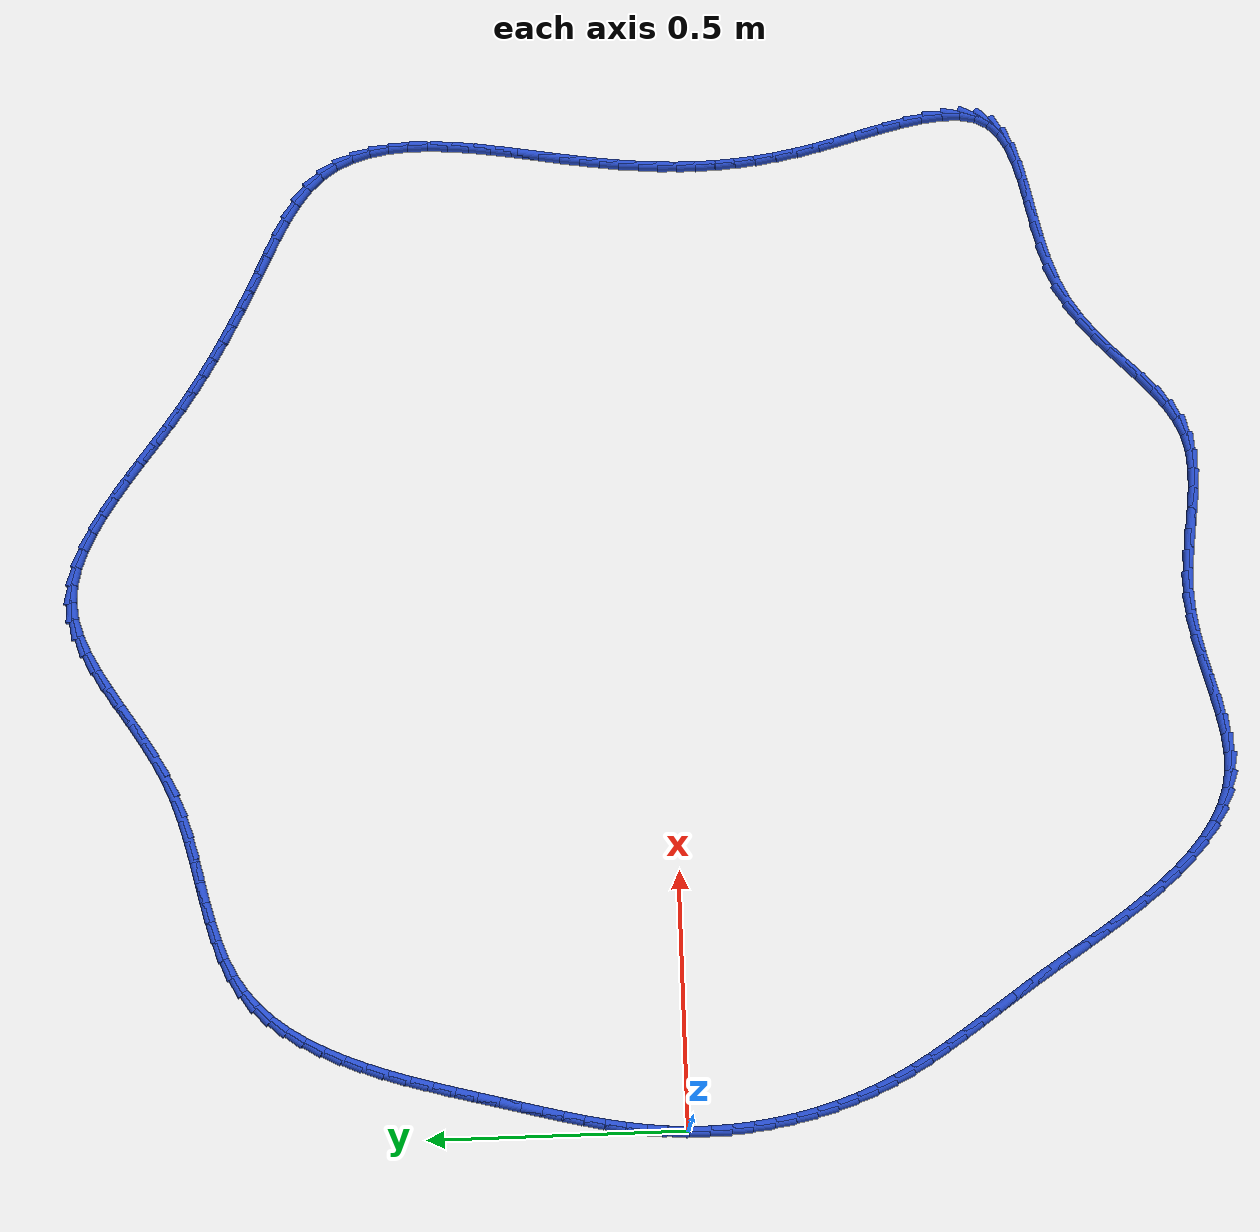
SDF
<sdf version="1.6">
 <world name="default">
  <light name="sun" type="directional">
   <pose>0 0 10 0 -0 0</pose>
   <diffuse>0.8 0.8 0.8 1</diffuse>
   <specular>0.2 0.2 0.2 1</specular>
   <attenuation>
    <range>1000</range>
    <constant>0.9</constant>
    <linear>0.01</linear>
    <quadratic>0.001</quadratic>
   </attenuation>
   <direction>-0.5 0.1 -0.9</direction>
  </light>
  <model name="ground_plane">
   <static>1</static>
   <link name="link">
    <collision name="collision">
     <geometry><plane><normal>0 0 1</normal><size>100 100</size></plane></geometry>
     <surface><friction><ode><mu>100</mu><mu2>50</mu2></ode></friction></surface>
    </collision>
    <visual name="visual">
     <cast_shadows>0</cast_shadows>
     <geometry><plane><normal>0 0 1</normal><size>100 100</size></plane></geometry>
     <material>
      <script><uri>file://media/materials/scripts/gazebo.material</uri><name>Gazebo/WhiteGlow</name></script>
     </material>
    </visual>
   </link>
  </model>
  <gravity>0 0 -9.8</gravity>
  <magnetic_field>6e-06 2.3e-05 -4.2e-05</magnetic_field>
  <atmosphere type="adiabatic"/>
  <physics name="default_physics" default="0" type="ode">
   <max_step_size>0.001</max_step_size>
   <real_time_factor>1</real_time_factor>
   <real_time_update_rate>1000</real_time_update_rate>
  </physics>
  <scene><ambient>0.4 0.4 0.4 1</ambient><background>0.7 0.7 0.7 1</background><shadows>1</shadows></scene>
  <spherical_coordinates>
   <surface_model>EARTH_WGS84</surface_model>
   <latitude_deg>0</latitude_deg>
   <longitude_deg>0</longitude_deg>
   <elevation>0</elevation>
   <heading_deg>0</heading_deg>
  </spherical_coordinates>
  <model name="line">
   <link name="link_0">
    <pose>-5.204170427930421e-18 -4.163336342344337e-17 0.01 0 1.57 1.513905280434671</pose>
    <collision name="collision">
     <geometry><cylinder><radius>0.01</radius><length>0.08</length></cylinder></geometry>
    </collision>
    <visual name="visual">
     <material>
      <script><name>Gazebo/Blue</name><uri>file://media/materials/scripts/gazebo.material</uri></script>
     </material>
     <geometry><cylinder><radius>0.01</radius><length>0.08</length></cylinder></geometry>
    </visual>
   </link>
   <link name="link_1">
    <pose>0.002293072764880472 0.04026289661467806 0.01 0 1.57 1.4680574297082787</pose>
    <collision name="collision">
     <geometry><cylinder><radius>0.01</radius><length>0.08</length></cylinder></geometry>
    </collision>
    <visual name="visual">
     <material>
      <script><name>Gazebo/Blue</name><uri>file://media/materials/scripts/gazebo.material</uri></script>
     </material>
     <geometry><cylinder><radius>0.01</radius><length>0.08</length></cylinder></geometry>
    </visual>
   </link>
   <link name="link_2">
    <pose>0.0064024168795074445 0.08012000642481716 0.01 0 1.57 1.4277513491622789</pose>
    <collision name="collision">
     <geometry><cylinder><radius>0.01</radius><length>0.08</length></cylinder></geometry>
    </collision>
    <visual name="visual">
     <material>
      <script><name>Gazebo/Blue</name><uri>file://media/materials/scripts/gazebo.material</uri></script>
     </material>
     <geometry><cylinder><radius>0.01</radius><length>0.08</length></cylinder></geometry>
    </visual>
   </link>
   <link name="link_3">
    <pose>0.01210741785367812 0.1197301782009352 0.01 0 1.57 1.393535114544863</pose>
    <collision name="collision">
     <geometry><cylinder><radius>0.01</radius><length>0.08</length></cylinder></geometry>
    </collision>
    <visual name="visual">
     <material>
      <script><name>Gazebo/Blue</name><uri>file://media/materials/scripts/gazebo.material</uri></script>
     </material>
     <geometry><cylinder><radius>0.01</radius><length>0.08</length></cylinder></geometry>
    </visual>
   </link>
   <link name="link_4">
    <pose>0.019187461197189743 0.15925226071355014 0.01 0 1.57 1.3657407606328948</pose>
    <collision name="collision">
     <geometry><cylinder><radius>0.01</radius><length>0.08</length></cylinder></geometry>
    </collision>
    <visual name="visual">
     <material>
      <script><name>Gazebo/Blue</name><uri>file://media/materials/scripts/gazebo.material</uri></script>
     </material>
     <geometry><cylinder><radius>0.01</radius><length>0.08</length></cylinder></geometry>
    </visual>
   </link>
   <link name="link_5">
    <pose>0.027421932419839513 0.19884510273317985 0.01 0 1.57 1.3445104145537299</pose>
    <collision name="collision">
     <geometry><cylinder><radius>0.01</radius><length>0.08</length></cylinder></geometry>
    </collision>
    <visual name="visual">
     <material>
      <script><name>Gazebo/Blue</name><uri>file://media/materials/scripts/gazebo.material</uri></script>
     </material>
     <geometry><cylinder><radius>0.01</radius><length>0.08</length></cylinder></geometry>
    </visual>
   </link>
   <link name="link_6">
    <pose>0.036590217031424656 0.2386675530303423 0.01 0 1.57 1.3298297836015076</pose>
    <collision name="collision">
     <geometry><cylinder><radius>0.01</radius><length>0.08</length></cylinder></geometry>
    </collision>
    <visual name="visual">
     <material>
      <script><name>Gazebo/Blue</name><uri>file://media/materials/scripts/gazebo.material</uri></script>
     </material>
     <geometry><cylinder><radius>0.01</radius><length>0.08</length></cylinder></geometry>
    </visual>
   </link>
   <link name="link_7">
    <pose>0.046471700541742406 0.2788784603755554 0.01 0 1.57 1.3215614664386257</pose>
    <collision name="collision">
     <geometry><cylinder><radius>0.01</radius><length>0.08</length></cylinder></geometry>
    </collision>
    <visual name="visual">
     <material>
      <script><name>Gazebo/Blue</name><uri>file://media/materials/scripts/gazebo.material</uri></script>
     </material>
     <geometry><cylinder><radius>0.01</radius><length>0.08</length></cylinder></geometry>
    </visual>
   </link>
   <link name="link_8">
    <pose>0.056845768460589974 0.3196366735393372 0.01 0 1.57 1.3194734919295483</pose>
    <collision name="collision">
     <geometry><cylinder><radius>0.01</radius><length>0.08</length></cylinder></geometry>
    </collision>
    <visual name="visual">
     <material>
      <script><name>Gazebo/Blue</name><uri>file://media/materials/scripts/gazebo.material</uri></script>
     </material>
     <geometry><cylinder><radius>0.01</radius><length>0.08</length></cylinder></geometry>
    </visual>
   </link>
   <link name="link_9">
    <pose>0.06749180629776459 0.36110104129220555 0.01 0 1.57 1.3211781342932702</pose>
    <collision name="collision">
     <geometry><cylinder><radius>0.01</radius><length>0.08</length></cylinder></geometry>
    </collision>
    <visual name="visual">
     <material>
      <script><name>Gazebo/Blue</name><uri>file://media/materials/scripts/gazebo.material</uri></script>
     </material>
     <geometry><cylinder><radius>0.01</radius><length>0.08</length></cylinder></geometry>
    </visual>
   </link>
   <link name="link_10">
    <pose>0.07826108646905851 0.40334423740519904 0.01 0 1.57 1.3181785002489284</pose>
    <collision name="collision">
     <geometry><cylinder><radius>0.01</radius><length>0.08</length></cylinder></geometry>
    </collision>
    <visual name="visual">
     <material>
      <script><name>Gazebo/Blue</name><uri>file://media/materials/scripts/gazebo.material</uri></script>
     </material>
     <geometry><cylinder><radius>0.01</radius><length>0.08</length></cylinder></geometry>
    </visual>
   </link>
   <link name="link_11">
    <pose>0.08929534082853424 0.44609074509093277 0.01 0 1.57 1.3084979038089992</pose>
    <collision name="collision">
     <geometry><cylinder><radius>0.01</radius><length>0.08</length></cylinder></geometry>
    </collision>
    <visual name="visual">
     <material>
      <script><name>Gazebo/Blue</name><uri>file://media/materials/scripts/gazebo.material</uri></script>
     </material>
     <geometry><cylinder><radius>0.01</radius><length>0.08</length></cylinder></geometry>
    </visual>
   </link>
   <link name="link_12">
    <pose>0.10080965139975946 0.48897711846378944 0.01 0 1.57 1.2920615907499067</pose>
    <collision name="collision">
     <geometry><cylinder><radius>0.01</radius><length>0.08</length></cylinder></geometry>
    </collision>
    <visual name="visual">
     <material>
      <script><name>Gazebo/Blue</name><uri>file://media/materials/scripts/gazebo.material</uri></script>
     </material>
     <geometry><cylinder><radius>0.01</radius><length>0.08</length></cylinder></geometry>
    </visual>
   </link>
   <link name="link_13">
    <pose>0.11301910020905238 0.5316399116348535 0.01 0 1.57 1.268539671049987</pose>
    <collision name="collision">
     <geometry><cylinder><radius>0.01</radius><length>0.08</length></cylinder></geometry>
    </collision>
    <visual name="visual">
     <material>
      <script><name>Gazebo/Blue</name><uri>file://media/materials/scripts/gazebo.material</uri></script>
     </material>
     <geometry><cylinder><radius>0.01</radius><length>0.08</length></cylinder></geometry>
    </visual>
   </link>
   <link name="link_14">
    <pose>0.12613876928273138 0.57371567871521 0.01 0 1.57 1.2373502660613087</pose>
    <collision name="collision">
     <geometry><cylinder><radius>0.01</radius><length>0.08</length></cylinder></geometry>
    </collision>
    <visual name="visual">
     <material>
      <script><name>Gazebo/Blue</name><uri>file://media/materials/scripts/gazebo.material</uri></script>
     </material>
     <geometry><cylinder><radius>0.01</radius><length>0.08</length></cylinder></geometry>
    </visual>
   </link>
   <link name="link_15">
    <pose>0.14038374064711473 0.6148409738159435 0.01 0 1.57 1.197656335810332</pose>
    <collision name="collision">
     <geometry><cylinder><radius>0.01</radius><length>0.08</length></cylinder></geometry>
    </collision>
    <visual name="visual">
     <material>
      <script><name>Gazebo/Blue</name><uri>file://media/materials/scripts/gazebo.material</uri></script>
     </material>
     <geometry><cylinder><radius>0.01</radius><length>0.08</length></cylinder></geometry>
    </visual>
   </link>
   <link name="link_16">
    <pose>0.15596909632852082 0.6546523510481392 0.01 0 1.57 1.1483673766644</pose>
    <collision name="collision">
     <geometry><cylinder><radius>0.01</radius><length>0.08</length></cylinder></geometry>
    </collision>
    <visual name="visual">
     <material>
      <script><name>Gazebo/Blue</name><uri>file://media/materials/scripts/gazebo.material</uri></script>
     </material>
     <geometry><cylinder><radius>0.01</radius><length>0.08</length></cylinder></geometry>
    </visual>
   </link>
   <link name="link_17">
    <pose>0.17310991835326794 0.6927863645228813 0.01 0 1.57 1.088165497358519</pose>
    <collision name="collision">
     <geometry><cylinder><radius>0.01</radius><length>0.08</length></cylinder></geometry>
    </collision>
    <visual name="visual">
     <material>
      <script><name>Gazebo/Blue</name><uri>file://media/materials/scripts/gazebo.material</uri></script>
     </material>
     <geometry><cylinder><radius>0.01</radius><length>0.08</length></cylinder></geometry>
    </visual>
   </link>
   <link name="link_18">
    <pose>0.19202128874767438 0.728879568351255 0.01 0 1.57 1.0155893693187203</pose>
    <collision name="collision">
     <geometry><cylinder><radius>0.01</radius><length>0.08</length></cylinder></geometry>
    </collision>
    <visual name="visual">
     <material>
      <script><name>Gazebo/Blue</name><uri>file://media/materials/scripts/gazebo.material</uri></script>
     </material>
     <geometry><cylinder><radius>0.01</radius><length>0.08</length></cylinder></geometry>
    </visual>
   </link>
   <link name="link_19">
    <pose>0.21291828953805852 0.7625685166443454 0.01 0 1.57 0.9292274954956832</pose>
    <collision name="collision">
     <geometry><cylinder><radius>0.01</radius><length>0.08</length></cylinder></geometry>
    </collision>
    <visual name="visual">
     <material>
      <script><name>Gazebo/Blue</name><uri>file://media/materials/scripts/gazebo.material</uri></script>
     </material>
     <geometry><cylinder><radius>0.01</radius><length>0.08</length></cylinder></geometry>
    </visual>
   </link>
   <link name="link_20">
    <pose>0.2360160027507386 0.7934897635132365 0.01 0 1.57 0.8280821252420515</pose>
    <collision name="collision">
     <geometry><cylinder><radius>0.01</radius><length>0.08</length></cylinder></geometry>
    </collision>
    <visual name="visual">
     <material>
      <script><name>Gazebo/Blue</name><uri>file://media/materials/scripts/gazebo.material</uri></script>
     </material>
     <geometry><cylinder><radius>0.01</radius><length>0.08</length></cylinder></geometry>
    </visual>
   </link>
   <link name="link_21">
    <pose>0.2615295104120331 0.8212798630690138 0.01 0 1.57 0.7121335410974271</pose>
    <collision name="collision">
     <geometry><cylinder><radius>0.01</radius><length>0.08</length></cylinder></geometry>
    </collision>
    <visual name="visual">
     <material>
      <script><name>Gazebo/Blue</name><uri>file://media/materials/scripts/gazebo.material</uri></script>
     </material>
     <geometry><cylinder><radius>0.01</radius><length>0.08</length></cylinder></geometry>
    </visual>
   </link>
   <link name="link_22">
    <pose>0.28967389454826 0.8455753694227616 0.01 0 1.57 0.5850457423293777</pose>
    <collision name="collision">
     <geometry><cylinder><radius>0.01</radius><length>0.08</length></cylinder></geometry>
    </collision>
    <visual name="visual">
     <material>
      <script><name>Gazebo/Blue</name><uri>file://media/materials/scripts/gazebo.material</uri></script>
     </material>
     <geometry><cylinder><radius>0.01</radius><length>0.08</length></cylinder></geometry>
    </visual>
   </link>
   <link name="link_23">
    <pose>0.3206270795238589 0.8660788840515742 0.01 0 1.57 0.46988482494122213</pose>
    <collision name="collision">
     <geometry><cylinder><radius>0.01</radius><length>0.08</length></cylinder></geometry>
    </collision>
    <visual name="visual">
     <material>
      <script><name>Gazebo/Blue</name><uri>file://media/materials/scripts/gazebo.material</uri></script>
     </material>
     <geometry><cylinder><radius>0.01</radius><length>0.08</length></cylinder></geometry>
    </visual>
   </link>
   <link name="link_24">
    <pose>0.35420761839157633 0.8831317872834248 0.01 0 1.57 0.37982766613788504</pose>
    <collision name="collision">
     <geometry><cylinder><radius>0.01</radius><length>0.08</length></cylinder></geometry>
    </collision>
    <visual name="visual">
     <material>
      <script><name>Gazebo/Blue</name><uri>file://media/materials/scripts/gazebo.material</uri></script>
     </material>
     <geometry><cylinder><radius>0.01</radius><length>0.08</length></cylinder></geometry>
    </visual>
   </link>
   <link name="link_25">
    <pose>0.39003258971823157 0.8974335782955515 0.01 0 1.57 0.3143938097577289</pose>
    <collision name="collision">
     <geometry><cylinder><radius>0.01</radius><length>0.08</length></cylinder></geometry>
    </collision>
    <visual name="visual">
     <material>
      <script><name>Gazebo/Blue</name><uri>file://media/materials/scripts/gazebo.material</uri></script>
     </material>
     <geometry><cylinder><radius>0.01</radius><length>0.08</length></cylinder></geometry>
    </visual>
   </link>
   <link name="link_26">
    <pose>0.4277168484675547 0.909687708697065 0.01 0 1.57 0.2717192743123202</pose>
    <collision name="collision">
     <geometry><cylinder><radius>0.01</radius><length>0.08</length></cylinder></geometry>
    </collision>
    <visual name="visual">
     <material>
      <script><name>Gazebo/Blue</name><uri>file://media/materials/scripts/gazebo.material</uri></script>
     </material>
     <geometry><cylinder><radius>0.01</radius><length>0.08</length></cylinder></geometry>
    </visual>
   </link>
   <link name="link_27">
    <pose>0.46687524960327537 0.9205976300970748 0.01 0 1.57 0.24982075747369306</pose>
    <collision name="collision">
     <geometry><cylinder><radius>0.01</radius><length>0.08</length></cylinder></geometry>
    </collision>
    <visual name="visual">
     <material>
      <script><name>Gazebo/Blue</name><uri>file://media/materials/scripts/gazebo.material</uri></script>
     </material>
     <geometry><cylinder><radius>0.01</radius><length>0.08</length></cylinder></geometry>
    </visual>
   </link>
   <link name="link_28">
    <pose>0.5071226480891243 0.9308667941046921 0.01 0 1.57 0.24713892666540466</pose>
    <collision name="collision">
     <geometry><cylinder><radius>0.01</radius><length>0.08</length></cylinder></geometry>
    </collision>
    <visual name="visual">
     <material>
      <script><name>Gazebo/Blue</name><uri>file://media/materials/scripts/gazebo.material</uri></script>
     </material>
     <geometry><cylinder><radius>0.01</radius><length>0.08</length></cylinder></geometry>
    </visual>
   </link>
   <link name="link_29">
    <pose>0.5480738988888312 0.9411986523290262 0.01 0 1.57 0.2626978691096048</pose>
    <collision name="collision">
     <geometry><cylinder><radius>0.01</radius><length>0.08</length></cylinder></geometry>
    </collision>
    <visual name="visual">
     <material>
      <script><name>Gazebo/Blue</name><uri>file://media/materials/scripts/gazebo.material</uri></script>
     </material>
     <geometry><cylinder><radius>0.01</radius><length>0.08</length></cylinder></geometry>
    </visual>
   </link>
   <link name="link_30">
    <pose>0.5893438569661262 0.9522966563791879 0.01 0 1.57 0.2960493335537899</pose>
    <collision name="collision">
     <geometry><cylinder><radius>0.01</radius><length>0.08</length></cylinder></geometry>
    </collision>
    <visual name="visual">
     <material>
      <script><name>Gazebo/Blue</name><uri>file://media/materials/scripts/gazebo.material</uri></script>
     </material>
     <geometry><cylinder><radius>0.01</radius><length>0.08</length></cylinder></geometry>
    </visual>
   </link>
   <link name="link_31">
    <pose>0.6305473772847394 0.9648642578642875 0.01 0 1.57 0.34707436338887726</pose>
    <collision name="collision">
     <geometry><cylinder><radius>0.01</radius><length>0.08</length></cylinder></geometry>
    </collision>
    <visual name="visual">
     <material>
      <script><name>Gazebo/Blue</name><uri>file://media/materials/scripts/gazebo.material</uri></script>
     </material>
     <geometry><cylinder><radius>0.01</radius><length>0.08</length></cylinder></geometry>
    </visual>
   </link>
   <link name="link_32">
    <pose>0.6712993148084009 0.9796049083934346 0.01 0 1.57 0.41561308090729066</pose>
    <collision name="collision">
     <geometry><cylinder><radius>0.01</radius><length>0.08</length></cylinder></geometry>
    </collision>
    <visual name="visual">
     <material>
      <script><name>Gazebo/Blue</name><uri>file://media/materials/scripts/gazebo.material</uri></script>
     </material>
     <geometry><cylinder><radius>0.01</radius><length>0.08</length></cylinder></geometry>
    </visual>
   </link>
   <link name="link_33">
    <pose>0.711214998484006 0.9972205382831679 0.01 0 1.57 0.490434120031888</pose>
    <collision name="collision">
     <geometry><cylinder><radius>0.01</radius><length>0.08</length></cylinder></geometry>
    </collision>
    <visual name="visual">
     <material>
      <script><name>Gazebo/Blue</name><uri>file://media/materials/scripts/gazebo.material</uri></script>
     </material>
     <geometry><cylinder><radius>0.01</radius><length>0.08</length></cylinder></geometry>
    </visual>
   </link>
   <link name="link_34">
    <pose>0.7500517704067763 1.0179572735863964 0.01 0 1.57 0.5462048074378624</pose>
    <collision name="collision">
     <geometry><cylinder><radius>0.01</radius><length>0.08</length></cylinder></geometry>
    </collision>
    <visual name="visual">
     <material>
      <script><name>Gazebo/Blue</name><uri>file://media/materials/scripts/gazebo.material</uri></script>
     </material>
     <geometry><cylinder><radius>0.01</radius><length>0.08</length></cylinder></geometry>
    </visual>
   </link>
   <link name="link_35">
    <pose>0.7879071554901473 1.0409693923068581 0.01 0 1.57 0.5804995807917855</pose>
    <collision name="collision">
     <geometry><cylinder><radius>0.01</radius><length>0.08</length></cylinder></geometry>
    </collision>
    <visual name="visual">
     <material>
      <script><name>Gazebo/Blue</name><uri>file://media/materials/scripts/gazebo.material</uri></script>
     </material>
     <geometry><cylinder><radius>0.01</radius><length>0.08</length></cylinder></geometry>
    </visual>
   </link>
   <link name="link_36">
    <pose>0.8249285554393954 1.065251088296617 0.01 0 1.57 0.5941176223363843</pose>
    <collision name="collision">
     <geometry><cylinder><radius>0.01</radius><length>0.08</length></cylinder></geometry>
    </collision>
    <visual name="visual">
     <material>
      <script><name>Gazebo/Blue</name><uri>file://media/materials/scripts/gazebo.material</uri></script>
     </material>
     <geometry><cylinder><radius>0.01</radius><length>0.08</length></cylinder></geometry>
    </visual>
   </link>
   <link name="link_37">
    <pose>0.8612633719597962 1.0897965554077376 0.01 0 1.57 0.5868349872010306</pose>
    <collision name="collision">
     <geometry><cylinder><radius>0.01</radius><length>0.08</length></cylinder></geometry>
    </collision>
    <visual name="visual">
     <material>
      <script><name>Gazebo/Blue</name><uri>file://media/materials/scripts/gazebo.material</uri></script>
     </material>
     <geometry><cylinder><radius>0.01</radius><length>0.08</length></cylinder></geometry>
    </visual>
   </link>
   <link name="link_38">
    <pose>0.8970590067566245 1.113599987492282 0.01 0 1.57 0.5571392559632566</pose>
    <collision name="collision">
     <geometry><cylinder><radius>0.01</radius><length>0.08</length></cylinder></geometry>
    </collision>
    <visual name="visual">
     <material>
      <script><name>Gazebo/Blue</name><uri>file://media/materials/scripts/gazebo.material</uri></script>
     </material>
     <geometry><cylinder><radius>0.01</radius><length>0.08</length></cylinder></geometry>
    </visual>
   </link>
   <link name="link_39">
    <pose>0.9324628615351568 1.135655578402315 0.01 0 1.57 0.5020618229438581</pose>
    <collision name="collision">
     <geometry><cylinder><radius>0.01</radius><length>0.08</length></cylinder></geometry>
    </collision>
    <visual name="visual">
     <material>
      <script><name>Gazebo/Blue</name><uri>file://media/materials/scripts/gazebo.material</uri></script>
     </material>
     <geometry><cylinder><radius>0.01</radius><length>0.08</length></cylinder></geometry>
    </visual>
   </link>
   <link name="link_40">
    <pose>0.967622338000668 1.1549575219898995 0.01 0 1.57 0.4172511850922168</pose>
    <collision name="collision">
     <geometry><cylinder><radius>0.01</radius><length>0.08</length></cylinder></geometry>
    </collision>
    <visual name="visual">
     <material>
      <script><name>Gazebo/Blue</name><uri>file://media/materials/scripts/gazebo.material</uri></script>
     </material>
     <geometry><cylinder><radius>0.01</radius><length>0.08</length></cylinder></geometry>
    </visual>
   </link>
   <link name="link_41">
    <pose>1.0026848378584337 1.1705000121070996 0.01 0 1.57 0.29780293614020903</pose>
    <collision name="collision">
     <geometry><cylinder><radius>0.01</radius><length>0.08</length></cylinder></geometry>
    </collision>
    <visual name="visual">
     <material>
      <script><name>Gazebo/Blue</name><uri>file://media/materials/scripts/gazebo.material</uri></script>
     </material>
     <geometry><cylinder><radius>0.01</radius><length>0.08</length></cylinder></geometry>
    </visual>
   </link>
   <link name="link_42">
    <pose>1.03779776281373 1.1812772426059786 0.01 0 1.57 0.1408359196409366</pose>
    <collision name="collision">
     <geometry><cylinder><radius>0.01</radius><length>0.08</length></cylinder></geometry>
    </collision>
    <visual name="visual">
     <material>
      <script><name>Gazebo/Blue</name><uri>file://media/materials/scripts/gazebo.material</uri></script>
     </material>
     <geometry><cylinder><radius>0.01</radius><length>0.08</length></cylinder></geometry>
    </visual>
   </link>
   <link name="link_43">
    <pose>1.0731085145718318 1.1862834073386006 0.01 0 1.57 -0.04283869534635073</pose>
    <collision name="collision">
     <geometry><cylinder><radius>0.01</radius><length>0.08</length></cylinder></geometry>
    </collision>
    <visual name="visual">
     <material>
      <script><name>Gazebo/Blue</name><uri>file://media/materials/scripts/gazebo.material</uri></script>
     </material>
     <geometry><cylinder><radius>0.01</radius><length>0.08</length></cylinder></geometry>
    </visual>
   </link>
   <link name="link_44">
    <pose>1.1087351744574678 1.1847562734200272 0.01 0 1.57 -0.20867135849247911</pose>
    <collision name="collision">
     <geometry><cylinder><radius>0.01</radius><length>0.08</length></cylinder></geometry>
    </collision>
    <visual name="visual">
     <material>
      <script><name>Gazebo/Blue</name><uri>file://media/materials/scripts/gazebo.material</uri></script>
     </material>
     <geometry><cylinder><radius>0.01</radius><length>0.08</length></cylinder></geometry>
    </visual>
   </link>
   <link name="link_45">
    <pose>1.1446492389579903 1.1771513325132588 0.01 0 1.57 -0.3416705830866303</pose>
    <collision name="collision">
     <geometry><cylinder><radius>0.01</radius><length>0.08</length></cylinder></geometry>
    </collision>
    <visual name="visual">
     <material>
      <script><name>Gazebo/Blue</name><uri>file://media/materials/scripts/gazebo.material</uri></script>
     </material>
     <geometry><cylinder><radius>0.01</radius><length>0.08</length></cylinder></geometry>
    </visual>
   </link>
   <link name="link_46">
    <pose>1.1807764894034296 1.1643038459101005 0.01 0 1.57 -0.4440825799264657</pose>
    <collision name="collision">
     <geometry><cylinder><radius>0.01</radius><length>0.08</length></cylinder></geometry>
    </collision>
    <visual name="visual">
     <material>
      <script><name>Gazebo/Blue</name><uri>file://media/materials/scripts/gazebo.material</uri></script>
     </material>
     <geometry><cylinder><radius>0.01</radius><length>0.08</length></cylinder></geometry>
    </visual>
   </link>
   <link name="link_47">
    <pose>1.2170426920898276 1.1470491997942642 0.01 0 1.57 -0.5205122893193966</pose>
    <collision name="collision">
     <geometry><cylinder><radius>0.01</radius><length>0.08</length></cylinder></geometry>
    </collision>
    <visual name="visual">
     <material>
      <script><name>Gazebo/Blue</name><uri>file://media/materials/scripts/gazebo.material</uri></script>
     </material>
     <geometry><cylinder><radius>0.01</radius><length>0.08</length></cylinder></geometry>
    </visual>
   </link>
   <link name="link_48">
    <pose>1.2533736133132252 1.126222780349462 0.01 0 1.57 -0.5754823118493644</pose>
    <collision name="collision">
     <geometry><cylinder><radius>0.01</radius><length>0.08</length></cylinder></geometry>
    </collision>
    <visual name="visual">
     <material>
      <script><name>Gazebo/Blue</name><uri>file://media/materials/scripts/gazebo.material</uri></script>
     </material>
     <geometry><cylinder><radius>0.01</radius><length>0.08</length></cylinder></geometry>
    </visual>
   </link>
   <link name="link_49">
    <pose>1.2896950193696632 1.1026599737594047 0.01 0 1.57 -0.6125284658679858</pose>
    <collision name="collision">
     <geometry><cylinder><radius>0.01</radius><length>0.08</length></cylinder></geometry>
    </collision>
    <visual name="visual">
     <material>
      <script><name>Gazebo/Blue</name><uri>file://media/materials/scripts/gazebo.material</uri></script>
     </material>
     <geometry><cylinder><radius>0.01</radius><length>0.08</length></cylinder></geometry>
    </visual>
   </link>
   <link name="link_50">
    <pose>1.3259326765551833 1.0771961662078033 0.01 0 1.57 -0.6340272139407414</pose>
    <collision name="collision">
     <geometry><cylinder><radius>0.01</radius><length>0.08</length></cylinder></geometry>
    </collision>
    <visual name="visual">
     <material>
      <script><name>Gazebo/Blue</name><uri>file://media/materials/scripts/gazebo.material</uri></script>
     </material>
     <geometry><cylinder><radius>0.01</radius><length>0.08</length></cylinder></geometry>
    </visual>
   </link>
   <link name="link_51">
    <pose>1.362012351165826 1.0506667438783697 0.01 0 1.57 -0.6412488032385681</pose>
    <collision name="collision">
     <geometry><cylinder><radius>0.01</radius><length>0.08</length></cylinder></geometry>
    </collision>
    <visual name="visual">
     <material>
      <script><name>Gazebo/Blue</name><uri>file://media/materials/scripts/gazebo.material</uri></script>
     </material>
     <geometry><cylinder><radius>0.01</radius><length>0.08</length></cylinder></geometry>
    </visual>
   </link>
   <link name="link_52">
    <pose>1.3978598094976329 1.023907092954815 0.01 0 1.57 -0.6344134094242865</pose>
    <collision name="collision">
     <geometry><cylinder><radius>0.01</radius><length>0.08</length></cylinder></geometry>
    </collision>
    <visual name="visual">
     <material>
      <script><name>Gazebo/Blue</name><uri>file://media/materials/scripts/gazebo.material</uri></script>
     </material>
     <geometry><cylinder><radius>0.01</radius><length>0.08</length></cylinder></geometry>
    </visual>
   </link>
   <link name="link_53">
    <pose>1.4334008178466449 0.9977525996208514 0.01 0 1.57 -0.6134081438822657</pose>
    <collision name="collision">
     <geometry><cylinder><radius>0.01</radius><length>0.08</length></cylinder></geometry>
    </collision>
    <visual name="visual">
     <material>
      <script><name>Gazebo/Blue</name><uri>file://media/materials/scripts/gazebo.material</uri></script>
     </material>
     <geometry><cylinder><radius>0.01</radius><length>0.08</length></cylinder></geometry>
    </visual>
   </link>
   <link name="link_54">
    <pose>1.4685715213510977 0.9729922845638402 0.01 0 1.57 -0.5864075788525958</pose>
    <collision name="collision">
     <geometry><cylinder><radius>0.01</radius><length>0.08</length></cylinder></geometry>
    </collision>
    <visual name="visual">
     <material>
      <script><name>Gazebo/Blue</name><uri>file://media/materials/scripts/gazebo.material</uri></script>
     </material>
     <geometry><cylinder><radius>0.01</radius><length>0.08</length></cylinder></geometry>
    </visual>
   </link>
   <link name="link_55">
    <pose>1.503439709040889 0.9498270745138628 0.01 0 1.57 -0.5600649396568915</pose>
    <collision name="collision">
     <geometry><cylinder><radius>0.01</radius><length>0.08</length></cylinder></geometry>
    </collision>
    <visual name="visual">
     <material>
      <script><name>Gazebo/Blue</name><uri>file://media/materials/scripts/gazebo.material</uri></script>
     </material>
     <geometry><cylinder><radius>0.01</radius><length>0.08</length></cylinder></geometry>
    </visual>
   </link>
   <link name="link_56">
    <pose>1.5381636290099951 0.9280537875994134 0.01 0 1.57 -0.5350830426676773</pose>
    <collision name="collision">
     <geometry><cylinder><radius>0.01</radius><length>0.08</length></cylinder></geometry>
    </collision>
    <visual name="visual">
     <material>
      <script><name>Gazebo/Blue</name><uri>file://media/materials/scripts/gazebo.material</uri></script>
     </material>
     <geometry><cylinder><radius>0.01</radius><length>0.08</length></cylinder></geometry>
    </visual>
   </link>
   <link name="link_57">
    <pose>1.5729033059908895 0.9074613051556425 0.01 0 1.57 -0.5120162792564805</pose>
    <collision name="collision">
     <geometry><cylinder><radius>0.01</radius><length>0.08</length></cylinder></geometry>
    </collision>
    <visual name="visual">
     <material>
      <script><name>Gazebo/Blue</name><uri>file://media/materials/scripts/gazebo.material</uri></script>
     </material>
     <geometry><cylinder><radius>0.01</radius><length>0.08</length></cylinder></geometry>
    </visual>
   </link>
   <link name="link_58">
    <pose>1.607818764716044 0.8878385085177005 0.01 0 1.57 -0.49135992198598105</pose>
    <collision name="collision">
     <geometry><cylinder><radius>0.01</radius><length>0.08</length></cylinder></geometry>
    </collision>
    <visual name="visual">
     <material>
      <script><name>Gazebo/Blue</name><uri>file://media/materials/scripts/gazebo.material</uri></script>
     </material>
     <geometry><cylinder><radius>0.01</radius><length>0.08</length></cylinder></geometry>
    </visual>
   </link>
   <link name="link_59">
    <pose>1.64307002991793 0.8689742790207376 0.01 0 1.57 -0.47351763720241713</pose>
    <collision name="collision">
     <geometry><cylinder><radius>0.01</radius><length>0.08</length></cylinder></geometry>
    </collision>
    <visual name="visual">
     <material>
      <script><name>Gazebo/Blue</name><uri>file://media/materials/scripts/gazebo.material</uri></script>
     </material>
     <geometry><cylinder><radius>0.01</radius><length>0.08</length></cylinder></geometry>
    </visual>
   </link>
   <link name="link_60">
    <pose>1.6788171263290208 0.8506574979999052 0.01 0 1.57 -0.4587785244799996</pose>
    <collision name="collision">
     <geometry><cylinder><radius>0.01</radius><length>0.08</length></cylinder></geometry>
    </collision>
    <visual name="visual">
     <material>
      <script><name>Gazebo/Blue</name><uri>file://media/materials/scripts/gazebo.material</uri></script>
     </material>
     <geometry><cylinder><radius>0.01</radius><length>0.08</length></cylinder></geometry>
    </visual>
   </link>
   <link name="link_61">
    <pose>1.7152200786817886 0.8326770467903528 0.01 0 1.57 -0.44730595617629876</pose>
    <collision name="collision">
     <geometry><cylinder><radius>0.01</radius><length>0.08</length></cylinder></geometry>
    </collision>
    <visual name="visual">
     <material>
      <script><name>Gazebo/Blue</name><uri>file://media/materials/scripts/gazebo.material</uri></script>
     </material>
     <geometry><cylinder><radius>0.01</radius><length>0.08</length></cylinder></geometry>
    </visual>
   </link>
   <link name="link_62">
    <pose>1.7524389117087047 0.8148218067272315 0.01 0 1.57 -0.4397778877596279</pose>
    <collision name="collision">
     <geometry><cylinder><radius>0.01</radius><length>0.08</length></cylinder></geometry>
    </collision>
    <visual name="visual">
     <material>
      <script><name>Gazebo/Blue</name><uri>file://media/materials/scripts/gazebo.material</uri></script>
     </material>
     <geometry><cylinder><radius>0.01</radius><length>0.08</length></cylinder></geometry>
    </visual>
   </link>
   <link name="link_63">
    <pose>1.7905946869582159 0.7968691628397468 0.01 0 1.57 -0.4478152844609477</pose>
    <collision name="collision">
     <geometry><cylinder><radius>0.01</radius><length>0.08</length></cylinder></geometry>
    </collision>
    <visual name="visual">
     <material>
      <script><name>Gazebo/Blue</name><uri>file://media/materials/scripts/gazebo.material</uri></script>
     </material>
     <geometry><cylinder><radius>0.01</radius><length>0.08</length></cylinder></geometry>
    </visual>
   </link>
   <link name="link_64">
    <pose>1.8290808573796944 0.7783818151596678 0.01 0 1.57 -0.48193903582845404</pose>
    <collision name="collision">
     <geometry><cylinder><radius>0.01</radius><length>0.08</length></cylinder></geometry>
    </collision>
    <visual name="visual">
     <material>
      <script><name>Gazebo/Blue</name><uri>file://media/materials/scripts/gazebo.material</uri></script>
     </material>
     <geometry><cylinder><radius>0.01</radius><length>0.08</length></cylinder></geometry>
    </visual>
   </link>
   <link name="link_65">
    <pose>1.866646157649573 0.7587322359768823 0.01 0 1.57 -0.5450507842750932</pose>
    <collision name="collision">
     <geometry><cylinder><radius>0.01</radius><length>0.08</length></cylinder></geometry>
    </collision>
    <visual name="visual">
     <material>
      <script><name>Gazebo/Blue</name><uri>file://media/materials/scripts/gazebo.material</uri></script>
     </material>
     <geometry><cylinder><radius>0.01</radius><length>0.08</length></cylinder></geometry>
    </visual>
   </link>
   <link name="link_66">
    <pose>1.9020170133869174 0.7372863151687983 0.01 0 1.57 -0.6424821381866102</pose>
    <collision name="collision">
     <geometry><cylinder><radius>0.01</radius><length>0.08</length></cylinder></geometry>
    </collision>
    <visual name="visual">
     <material>
      <script><name>Gazebo/Blue</name><uri>file://media/materials/scripts/gazebo.material</uri></script>
     </material>
     <geometry><cylinder><radius>0.01</radius><length>0.08</length></cylinder></geometry>
    </visual>
   </link>
   <link name="link_67">
    <pose>1.933919850210792 0.7134099426128232 0.01 0 1.57 -0.781323579169599</pose>
    <collision name="collision">
     <geometry><cylinder><radius>0.01</radius><length>0.08</length></cylinder></geometry>
    </collision>
    <visual name="visual">
     <material>
      <script><name>Gazebo/Blue</name><uri>file://media/materials/scripts/gazebo.material</uri></script>
     </material>
     <geometry><cylinder><radius>0.01</radius><length>0.08</length></cylinder></geometry>
    </visual>
   </link>
   <link name="link_68">
    <pose>1.9610811804362533 0.6864690576400629 0.01 0 1.57 -0.9554181284804882</pose>
    <collision name="collision">
     <geometry><cylinder><radius>0.01</radius><length>0.08</length></cylinder></geometry>
    </collision>
    <visual name="visual">
     <material>
      <script><name>Gazebo/Blue</name><uri>file://media/materials/scripts/gazebo.material</uri></script>
     </material>
     <geometry><cylinder><radius>0.01</radius><length>0.08</length></cylinder></geometry>
    </visual>
   </link>
   <link name="link_69">
    <pose>1.9825940668032185 0.6560386896911992 0.01 0 1.57 -1.1231324074281746</pose>
    <collision name="collision">
     <geometry><cylinder><radius>0.01</radius><length>0.08</length></cylinder></geometry>
    </collision>
    <visual name="visual">
     <material>
      <script><name>Gazebo/Blue</name><uri>file://media/materials/scripts/gazebo.material</uri></script>
     </material>
     <geometry><cylinder><radius>0.01</radius><length>0.08</length></cylinder></geometry>
    </visual>
   </link>
   <link name="link_70">
    <pose>1.9987558151451228 0.6223808004904414 0.01 0 1.57 -1.2690595300823144</pose>
    <collision name="collision">
     <geometry><cylinder><radius>0.01</radius><length>0.08</length></cylinder></geometry>
    </collision>
    <visual name="visual">
     <material>
      <script><name>Gazebo/Blue</name><uri>file://media/materials/scripts/gazebo.material</uri></script>
     </material>
     <geometry><cylinder><radius>0.01</radius><length>0.08</length></cylinder></geometry>
    </visual>
   </link>
   <link name="link_71">
    <pose>2.0101106662156147 0.5858982100069328 0.01 0 1.57 -1.390478721852128</pose>
    <collision name="collision">
     <geometry><cylinder><radius>0.01</radius><length>0.08</length></cylinder></geometry>
    </collision>
    <visual name="visual">
     <material>
      <script><name>Gazebo/Blue</name><uri>file://media/materials/scripts/gazebo.material</uri></script>
     </material>
     <geometry><cylinder><radius>0.01</radius><length>0.08</length></cylinder></geometry>
    </visual>
   </link>
   <link name="link_72">
    <pose>2.017202860768345 0.5469937382098173 0.01 0 1.57 -1.4885412959173654</pose>
    <collision name="collision">
     <geometry><cylinder><radius>0.01</radius><length>0.08</length></cylinder></geometry>
    </collision>
    <visual name="visual">
     <material>
      <script><name>Gazebo/Blue</name><uri>file://media/materials/scripts/gazebo.material</uri></script>
     </material>
     <geometry><cylinder><radius>0.01</radius><length>0.08</length></cylinder></geometry>
    </visual>
   </link>
   <link name="link_73">
    <pose>2.020576639556963 0.5060702050682382 0.01 0 1.57 -1.5661041930075164</pose>
    <collision name="collision">
     <geometry><cylinder><radius>0.01</radius><length>0.08</length></cylinder></geometry>
    </collision>
    <visual name="visual">
     <material>
      <script><name>Gazebo/Blue</name><uri>file://media/materials/scripts/gazebo.material</uri></script>
     </material>
     <geometry><cylinder><radius>0.01</radius><length>0.08</length></cylinder></geometry>
    </visual>
   </link>
   <link name="link_74">
    <pose>2.020776243335117 0.4635304305513381 0.01 0 1.57 1.51530699549678</pose>
    <collision name="collision">
     <geometry><cylinder><radius>0.01</radius><length>0.08</length></cylinder></geometry>
    </collision>
    <visual name="visual">
     <material>
      <script><name>Gazebo/Blue</name><uri>file://media/materials/scripts/gazebo.material</uri></script>
     </material>
     <geometry><cylinder><radius>0.01</radius><length>0.08</length></cylinder></geometry>
    </visual>
   </link>
   <link name="link_75">
    <pose>2.0183459128564576 0.41977723462826144 0.01 0 1.57 1.4698027008228884</pose>
    <collision name="collision">
     <geometry><cylinder><radius>0.01</radius><length>0.08</length></cylinder></geometry>
    </collision>
    <visual name="visual">
     <material>
      <script><name>Gazebo/Blue</name><uri>file://media/materials/scripts/gazebo.material</uri></script>
     </material>
     <geometry><cylinder><radius>0.01</radius><length>0.08</length></cylinder></geometry>
    </visual>
   </link>
   <link name="link_76">
    <pose>2.013829888874634 0.37521343726815104 0.01 0 1.57 1.4369064983368984</pose>
    <collision name="collision">
     <geometry><cylinder><radius>0.01</radius><length>0.08</length></cylinder></geometry>
    </collision>
    <visual name="visual">
     <material>
      <script><name>Gazebo/Blue</name><uri>file://media/materials/scripts/gazebo.material</uri></script>
     </material>
     <geometry><cylinder><radius>0.01</radius><length>0.08</length></cylinder></geometry>
    </visual>
   </link>
   <link name="link_77">
    <pose>2.0077724121432956 0.33024185844015 0.01 0 1.57 1.4152113690932766</pose>
    <collision name="collision">
     <geometry><cylinder><radius>0.01</radius><length>0.08</length></cylinder></geometry>
    </collision>
    <visual name="visual">
     <material>
      <script><name>Gazebo/Blue</name><uri>file://media/materials/scripts/gazebo.material</uri></script>
     </material>
     <geometry><cylinder><radius>0.01</radius><length>0.08</length></cylinder></geometry>
    </visual>
   </link>
   <link name="link_78">
    <pose>2.000717723416092 0.2852653181134027 0.01 0 1.57 1.403948333308814</pose>
    <collision name="collision">
     <geometry><cylinder><radius>0.01</radius><length>0.08</length></cylinder></geometry>
    </collision>
    <visual name="visual">
     <material>
      <script><name>Gazebo/Blue</name><uri>file://media/materials/scripts/gazebo.material</uri></script>
     </material>
     <geometry><cylinder><radius>0.01</radius><length>0.08</length></cylinder></geometry>
    </visual>
   </link>
   <link name="link_79">
    <pose>1.993210063446673 0.24068663625705145 0.01 0 1.57 1.4029805660764292</pose>
    <collision name="collision">
     <geometry><cylinder><radius>0.01</radius><length>0.08</length></cylinder></geometry>
    </collision>
    <visual name="visual">
     <material>
      <script><name>Gazebo/Blue</name><uri>file://media/materials/scripts/gazebo.material</uri></script>
     </material>
     <geometry><cylinder><radius>0.01</radius><length>0.08</length></cylinder></geometry>
    </visual>
   </link>
   <link name="link_80">
    <pose>1.9857936729886876 0.19690863284024063 0.01 0 1.57 1.4121566011729525</pose>
    <collision name="collision">
     <geometry><cylinder><radius>0.01</radius><length>0.08</length></cylinder></geometry>
    </collision>
    <visual name="visual">
     <material>
      <script><name>Gazebo/Blue</name><uri>file://media/materials/scripts/gazebo.material</uri></script>
     </material>
     <geometry><cylinder><radius>0.01</radius><length>0.08</length></cylinder></geometry>
    </visual>
   </link>
   <link name="link_81">
    <pose>1.9789736565380283 0.15427928460389026 0.01 0 1.57 1.42732540284289</pose>
    <collision name="collision">
     <geometry><cylinder><radius>0.01</radius><length>0.08</length></cylinder></geometry>
    </collision>
    <visual name="visual">
     <material>
      <script><name>Gazebo/Blue</name><uri>file://media/materials/scripts/gazebo.material</uri></script>
     </material>
     <geometry><cylinder><radius>0.01</radius><length>0.08</length></cylinder></geometry>
    </visual>
   </link>
   <link name="link_82">
    <pose>1.9729747149742998 0.11275362730775111 0.01 0 1.57 1.4465460691664207</pose>
    <collision name="collision">
     <geometry><cylinder><radius>0.01</radius><length>0.08</length></cylinder></geometry>
    </collision>
    <visual name="visual">
     <material>
      <script><name>Gazebo/Blue</name><uri>file://media/materials/scripts/gazebo.material</uri></script>
     </material>
     <geometry><cylinder><radius>0.01</radius><length>0.08</length></cylinder></geometry>
    </visual>
   </link>
   <link name="link_83">
    <pose>1.9678992482779107 0.072115311492069 0.01 0 1.57 1.4698075770740986</pose>
    <collision name="collision">
     <geometry><cylinder><radius>0.01</radius><length>0.08</length></cylinder></geometry>
    </collision>
    <visual name="visual">
     <material>
      <script><name>Gazebo/Blue</name><uri>file://media/materials/scripts/gazebo.material</uri></script>
     </material>
     <geometry><cylinder><radius>0.01</radius><length>0.08</length></cylinder></geometry>
    </visual>
   </link>
   <link name="link_84">
    <pose>1.9638491483177754 0.032147275659804894 0.01 0 1.57 1.4969625499661707</pose>
    <collision name="collision">
     <geometry><cylinder><radius>0.01</radius><length>0.08</length></cylinder></geometry>
    </collision>
    <visual name="visual">
     <material>
      <script><name>Gazebo/Blue</name><uri>file://media/materials/scripts/gazebo.material</uri></script>
     </material>
     <geometry><cylinder><radius>0.01</radius><length>0.08</length></cylinder></geometry>
    </visual>
   </link>
   <link name="link_85">
    <pose>1.9609263069628102 -0.007367541686078638 0.01 0 1.57 1.5277031477358884</pose>
    <collision name="collision">
     <geometry><cylinder><radius>0.01</radius><length>0.08</length></cylinder></geometry>
    </collision>
    <visual name="visual">
     <material>
      <script><name>Gazebo/Blue</name><uri>file://media/materials/scripts/gazebo.material</uri></script>
     </material>
     <geometry><cylinder><radius>0.01</radius><length>0.08</length></cylinder></geometry>
    </visual>
   </link>
   <link name="link_86">
    <pose>1.959232616081929 -0.04664620204262017 0.01 0 1.57 1.5615593873324645</pose>
    <collision name="collision">
     <geometry><cylinder><radius>0.01</radius><length>0.08</length></cylinder></geometry>
    </collision>
    <visual name="visual">
     <material>
      <script><name>Gazebo/Blue</name><uri>file://media/materials/scripts/gazebo.material</uri></script>
     </material>
     <geometry><cylinder><radius>0.01</radius><length>0.08</length></cylinder></geometry>
    </visual>
   </link>
   <link name="link_87">
    <pose>1.9588699675440464 -0.08590576690685787 0.01 0 1.57 -1.5436779726283616</pose>
    <collision name="collision">
     <geometry><cylinder><radius>0.01</radius><length>0.08</length></cylinder></geometry>
    </collision>
    <visual name="visual">
     <material>
      <script><name>Gazebo/Blue</name><uri>file://media/materials/scripts/gazebo.material</uri></script>
     </material>
     <geometry><cylinder><radius>0.01</radius><length>0.08</length></cylinder></geometry>
    </visual>
   </link>
   <link name="link_88">
    <pose>1.959940253218078 -0.12536329777583005 0.01 0 1.57 -1.5055531009432017</pose>
    <collision name="collision">
     <geometry><cylinder><radius>0.01</radius><length>0.08</length></cylinder></geometry>
    </collision>
    <visual name="visual">
     <material>
      <script><name>Gazebo/Blue</name><uri>file://media/materials/scripts/gazebo.material</uri></script>
     </material>
     <geometry><cylinder><radius>0.01</radius><length>0.08</length></cylinder></geometry>
    </visual>
   </link>
   <link name="link_89">
    <pose>1.9625453649729387 -0.16523585614657557 0.01 0 1.57 -1.466452154099231</pose>
    <collision name="collision">
     <geometry><cylinder><radius>0.01</radius><length>0.08</length></cylinder></geometry>
    </collision>
    <visual name="visual">
     <material>
      <script><name>Gazebo/Blue</name><uri>file://media/materials/scripts/gazebo.material</uri></script>
     </material>
     <geometry><cylinder><radius>0.01</radius><length>0.08</length></cylinder></geometry>
    </visual>
   </link>
   <link name="link_90">
    <pose>1.9667871946775417 -0.20574050351613113 0.01 0 1.57 -1.427175575508351</pose>
    <collision name="collision">
     <geometry><cylinder><radius>0.01</radius><length>0.08</length></cylinder></geometry>
    </collision>
    <visual name="visual">
     <material>
      <script><name>Gazebo/Blue</name><uri>file://media/materials/scripts/gazebo.material</uri></script>
     </material>
     <geometry><cylinder><radius>0.01</radius><length>0.08</length></cylinder></geometry>
    </visual>
   </link>
   <link name="link_91">
    <pose>1.9727676342008045 -0.24709430138153576 0.01 0 1.57 -1.3884746018303582</pose>
    <collision name="collision">
     <geometry><cylinder><radius>0.01</radius><length>0.08</length></cylinder></geometry>
    </collision>
    <visual name="visual">
     <material>
      <script><name>Gazebo/Blue</name><uri>file://media/materials/scripts/gazebo.material</uri></script>
     </material>
     <geometry><cylinder><radius>0.01</radius><length>0.08</length></cylinder></geometry>
    </visual>
   </link>
   <link name="link_92">
    <pose>1.9805885754116395 -0.2895143112398276 0.01 0 1.57 -1.3510048448109573</pose>
    <collision name="collision">
     <geometry><cylinder><radius>0.01</radius><length>0.08</length></cylinder></geometry>
    </collision>
    <visual name="visual">
     <material>
      <script><name>Gazebo/Blue</name><uri>file://media/materials/scripts/gazebo.material</uri></script>
     </material>
     <geometry><cylinder><radius>0.01</radius><length>0.08</length></cylinder></geometry>
    </visual>
   </link>
   <link name="link_93">
    <pose>1.9903519101789628 -0.3332175945880449 0.01 0 1.57 -1.316937560966134</pose>
    <collision name="collision">
     <geometry><cylinder><radius>0.01</radius><length>0.08</length></cylinder></geometry>
    </collision>
    <visual name="visual">
     <material>
      <script><name>Gazebo/Blue</name><uri>file://media/materials/scripts/gazebo.material</uri></script>
     </material>
     <geometry><cylinder><radius>0.01</radius><length>0.08</length></cylinder></geometry>
    </visual>
   </link>
   <link name="link_94">
    <pose>2.0020586137711405 -0.3783377219072846 0.01 0 1.57 -1.2988861251615438</pose>
    <collision name="collision">
     <geometry><cylinder><radius>0.01</radius><length>0.08</length></cylinder></geometry>
    </collision>
    <visual name="visual">
     <material>
      <script><name>Gazebo/Blue</name><uri>file://media/materials/scripts/gazebo.material</uri></script>
     </material>
     <geometry><cylinder><radius>0.01</radius><length>0.08</length></cylinder></geometry>
    </visual>
   </link>
   <link name="link_95">
    <pose>2.0148796307663535 -0.4243215569801443 0.01 0 1.57 -1.3012096727508344</pose>
    <collision name="collision">
     <geometry><cylinder><radius>0.01</radius><length>0.08</length></cylinder></geometry>
    </collision>
    <visual name="visual">
     <material>
      <script><name>Gazebo/Blue</name><uri>file://media/materials/scripts/gazebo.material</uri></script>
     </material>
     <geometry><cylinder><radius>0.01</radius><length>0.08</length></cylinder></geometry>
    </visual>
   </link>
   <link name="link_96">
    <pose>2.027578178514653 -0.47027863989501856 0.01 0 1.57 -1.3242073748985568</pose>
    <collision name="collision">
     <geometry><cylinder><radius>0.01</radius><length>0.08</length></cylinder></geometry>
    </collision>
    <visual name="visual">
     <material>
      <script><name>Gazebo/Blue</name><uri>file://media/materials/scripts/gazebo.material</uri></script>
     </material>
     <geometry><cylinder><radius>0.01</radius><length>0.08</length></cylinder></geometry>
    </visual>
   </link>
   <link name="link_97">
    <pose>2.038914649125346 -0.5153161733426989 0.01 0 1.57 -1.3714051287247226</pose>
    <collision name="collision">
     <geometry><cylinder><radius>0.01</radius><length>0.08</length></cylinder></geometry>
    </collision>
    <visual name="visual">
     <material>
      <script><name>Gazebo/Blue</name><uri>file://media/materials/scripts/gazebo.material</uri></script>
     </material>
     <geometry><cylinder><radius>0.01</radius><length>0.08</length></cylinder></geometry>
    </visual>
   </link>
   <link name="link_98">
    <pose>2.047649434707736 -0.5585413600139763 0.01 0 1.57 -1.45061114638508</pose>
    <collision name="collision">
     <geometry><cylinder><radius>0.01</radius><length>0.08</length></cylinder></geometry>
    </collision>
    <visual name="visual">
     <material>
      <script><name>Gazebo/Blue</name><uri>file://media/materials/scripts/gazebo.material</uri></script>
     </material>
     <geometry><cylinder><radius>0.01</radius><length>0.08</length></cylinder></geometry>
    </visual>
   </link>
   <link name="link_99">
    <pose>2.0525429273711286 -0.5990614025996428 0.01 0 1.57 1.5657205989556948</pose>
    <collision name="collision">
     <geometry><cylinder><radius>0.01</radius><length>0.08</length></cylinder></geometry>
    </collision>
    <visual name="visual">
     <material>
      <script><name>Gazebo/Blue</name><uri>file://media/materials/scripts/gazebo.material</uri></script>
     </material>
     <geometry><cylinder><radius>0.01</radius><length>0.08</length></cylinder></geometry>
    </visual>
   </link>
   <link name="link_100">
    <pose>2.05235551922483 -0.6359835037904885 0.01 0 1.57 1.3727591287541245</pose>
    <collision name="collision">
     <geometry><cylinder><radius>0.01</radius><length>0.08</length></cylinder></geometry>
    </collision>
    <visual name="visual">
     <material>
      <script><name>Gazebo/Blue</name><uri>file://media/materials/scripts/gazebo.material</uri></script>
     </material>
     <geometry><cylinder><radius>0.01</radius><length>0.08</length></cylinder></geometry>
    </visual>
   </link>
   <link name="link_101">
    <pose>2.045847602378144 -0.6684148662773048 0.01 0 1.57 1.0913451657512743</pose>
    <collision name="collision">
     <geometry><cylinder><radius>0.01</radius><length>0.08</length></cylinder></geometry>
    </collision>
    <visual name="visual">
     <material>
      <script><name>Gazebo/Blue</name><uri>file://media/materials/scripts/gazebo.material</uri></script>
     </material>
     <geometry><cylinder><radius>0.01</radius><length>0.08</length></cylinder></geometry>
    </visual>
   </link>
   <link name="link_102">
    <pose>2.0317834404854804 -0.6954658339065443 0.01 0 1.57 0.7675276500604542</pose>
    <collision name="collision">
     <geometry><cylinder><radius>0.01</radius><length>0.08</length></cylinder></geometry>
    </collision>
    <visual name="visual">
     <material>
      <script><name>Gazebo/Blue</name><uri>file://media/materials/scripts/gazebo.material</uri></script>
     </material>
     <geometry><cylinder><radius>0.01</radius><length>0.08</length></cylinder></geometry>
    </visual>
   </link>
   <link name="link_103">
    <pose>2.009643750027543 -0.7168280403690866 0.01 0 1.57 0.5177478909237357</pose>
    <collision name="collision">
     <geometry><cylinder><radius>0.01</radius><length>0.08</length></cylinder></geometry>
    </collision>
    <visual name="visual">
     <material>
      <script><name>Gazebo/Blue</name><uri>file://media/materials/scripts/gazebo.material</uri></script>
     </material>
     <geometry><cylinder><radius>0.01</radius><length>0.08</length></cylinder></geometry>
    </visual>
   </link>
   <link name="link_104">
    <pose>1.9804593258913652 -0.7334507664786885 0.01 0 1.57 0.35559265468118156</pose>
    <collision name="collision">
     <geometry><cylinder><radius>0.01</radius><length>0.08</length></cylinder></geometry>
    </collision>
    <visual name="visual">
     <material>
      <script><name>Gazebo/Blue</name><uri>file://media/materials/scripts/gazebo.material</uri></script>
     </material>
     <geometry><cylinder><radius>0.01</radius><length>0.08</length></cylinder></geometry>
    </visual>
   </link>
   <link name="link_105">
    <pose>1.9454633936827843 -0.746447534038492 0.01 0 1.57 0.25897876699022415</pose>
    <collision name="collision">
     <geometry><cylinder><radius>0.01</radius><length>0.08</length></cylinder></geometry>
    </collision>
    <visual name="visual">
     <material>
      <script><name>Gazebo/Blue</name><uri>file://media/materials/scripts/gazebo.material</uri></script>
     </material>
     <geometry><cylinder><radius>0.01</radius><length>0.08</length></cylinder></geometry>
    </visual>
   </link>
   <link name="link_106">
    <pose>1.9058891790076355 -0.7569318648516398 0.01 0 1.57 0.2086065883803087</pose>
    <collision name="collision">
     <geometry><cylinder><radius>0.01</radius><length>0.08</length></cylinder></geometry>
    </collision>
    <visual name="visual">
     <material>
      <script><name>Gazebo/Blue</name><uri>file://media/materials/scripts/gazebo.material</uri></script>
     </material>
     <geometry><cylinder><radius>0.01</radius><length>0.08</length></cylinder></geometry>
    </visual>
   </link>
   <link name="link_107">
    <pose>1.862969907471753 -0.7660172807212743 0.01 0 1.57 0.19298881451127234</pose>
    <collision name="collision">
     <geometry><cylinder><radius>0.01</radius><length>0.08</length></cylinder></geometry>
    </collision>
    <visual name="visual">
     <material>
      <script><name>Gazebo/Blue</name><uri>file://media/materials/scripts/gazebo.material</uri></script>
     </material>
     <geometry><cylinder><radius>0.01</radius><length>0.08</length></cylinder></geometry>
    </visual>
   </link>
   <link name="link_108">
    <pose>1.8179388046809732 -0.7748173034505381 0.01 0 1.57 0.20672332410948482</pose>
    <collision name="collision">
     <geometry><cylinder><radius>0.01</radius><length>0.08</length></cylinder></geometry>
    </collision>
    <visual name="visual">
     <material>
      <script><name>Gazebo/Blue</name><uri>file://media/materials/scripts/gazebo.material</uri></script>
     </material>
     <geometry><cylinder><radius>0.01</radius><length>0.08</length></cylinder></geometry>
    </visual>
   </link>
   <link name="link_109">
    <pose>1.7720290962411311 -0.784445454842574 0.01 0 1.57 0.24871525942448186</pose>
    <collision name="collision">
     <geometry><cylinder><radius>0.01</radius><length>0.08</length></cylinder></geometry>
    </collision>
    <visual name="visual">
     <material>
      <script><name>Gazebo/Blue</name><uri>file://media/materials/scripts/gazebo.material</uri></script>
     </material>
     <geometry><cylinder><radius>0.01</radius><length>0.08</length></cylinder></geometry>
    </visual>
   </link>
   <link name="link_110">
    <pose>1.7264740077580607 -0.7960152567005241 0.01 0 1.57 0.3211204949917531</pose>
    <collision name="collision">
     <geometry><cylinder><radius>0.01</radius><length>0.08</length></cylinder></geometry>
    </collision>
    <visual name="visual">
     <material>
      <script><name>Gazebo/Blue</name><uri>file://media/materials/scripts/gazebo.material</uri></script>
     </material>
     <geometry><cylinder><radius>0.01</radius><length>0.08</length></cylinder></geometry>
    </visual>
   </link>
   <link name="link_111">
    <pose>1.6825067648376004 -0.8106402308275313 0.01 0 1.57 0.4281188885713341</pose>
    <collision name="collision">
     <geometry><cylinder><radius>0.01</radius><length>0.08</length></cylinder></geometry>
    </collision>
    <visual name="visual">
     <material>
      <script><name>Gazebo/Blue</name><uri>file://media/materials/scripts/gazebo.material</uri></script>
     </material>
     <geometry><cylinder><radius>0.01</radius><length>0.08</length></cylinder></geometry>
    </visual>
   </link>
   <link name="link_112">
    <pose>1.641350854350439 -0.8294215746643472 0.01 0 1.57 0.5503155385285533</pose>
    <collision name="collision">
     <geometry><cylinder><radius>0.01</radius><length>0.08</length></cylinder></geometry>
    </collision>
    <visual name="visual">
     <material>
      <script><name>Gazebo/Blue</name><uri>file://media/materials/scripts/gazebo.material</uri></script>
     </material>
     <geometry><cylinder><radius>0.01</radius><length>0.08</length></cylinder></geometry>
    </visual>
   </link>
   <link name="link_113">
    <pose>1.6035572611906457 -0.8526094348792348 0.01 0 1.57 0.6475923498457024</pose>
    <collision name="collision">
     <geometry><cylinder><radius>0.01</radius><length>0.08</length></cylinder></geometry>
    </collision>
    <visual name="visual">
     <material>
      <script><name>Gazebo/Blue</name><uri>file://media/materials/scripts/gazebo.material</uri></script>
     </material>
     <geometry><cylinder><radius>0.01</radius><length>0.08</length></cylinder></geometry>
    </visual>
   </link>
   <link name="link_114">
    <pose>1.5685804557772969 -0.8790663198532378 0.01 0 1.57 0.7145843804362589</pose>
    <collision name="collision">
     <geometry><cylinder><radius>0.01</radius><length>0.08</length></cylinder></geometry>
    </collision>
    <visual name="visual">
     <material>
      <script><name>Gazebo/Blue</name><uri>file://media/materials/scripts/gazebo.material</uri></script>
     </material>
     <geometry><cylinder><radius>0.01</radius><length>0.08</length></cylinder></geometry>
    </visual>
   </link>
   <link name="link_115">
    <pose>1.5357739607521996 -0.9075269886271589 0.01 0 1.57 0.7509642620244827</pose>
    <collision name="collision">
     <geometry><cylinder><radius>0.01</radius><length>0.08</length></cylinder></geometry>
    </collision>
    <visual name="visual">
     <material>
      <script><name>Gazebo/Blue</name><uri>file://media/materials/scripts/gazebo.material</uri></script>
     </material>
     <geometry><cylinder><radius>0.01</radius><length>0.08</length></cylinder></geometry>
    </visual>
   </link>
   <link name="link_116">
    <pose>1.5044912987571641 -0.9367262002418002 0.01 0 1.57 0.7560758866484426</pose>
    <collision name="collision">
     <geometry><cylinder><radius>0.01</radius><length>0.08</length></cylinder></geometry>
    </collision>
    <visual name="visual">
     <material>
      <script><name>Gazebo/Blue</name><uri>file://media/materials/scripts/gazebo.material</uri></script>
     </material>
     <geometry><cylinder><radius>0.01</radius><length>0.08</length></cylinder></geometry>
    </visual>
   </link>
   <link name="link_117">
    <pose>1.4740859924339973 -0.9653987137379645 0.01 0 1.57 0.7277309756041553</pose>
    <collision name="collision">
     <geometry><cylinder><radius>0.01</radius><length>0.08</length></cylinder></geometry>
    </collision>
    <visual name="visual">
     <material>
      <script><name>Gazebo/Blue</name><uri>file://media/materials/scripts/gazebo.material</uri></script>
     </material>
     <geometry><cylinder><radius>0.01</radius><length>0.08</length></cylinder></geometry>
    </visual>
   </link>
   <link name="link_118">
    <pose>1.4439115644245089 -0.9922792881564549 0.01 0 1.57 0.6616773613531324</pose>
    <collision name="collision">
     <geometry><cylinder><radius>0.01</radius><length>0.08</length></cylinder></geometry>
    </collision>
    <visual name="visual">
     <material>
      <script><name>Gazebo/Blue</name><uri>file://media/materials/scripts/gazebo.material</uri></script>
     </material>
     <geometry><cylinder><radius>0.01</radius><length>0.08</length></cylinder></geometry>
    </visual>
   </link>
   <link name="link_119">
    <pose>1.4133215373705061 -1.0161026825380737 0.01 0 1.57 0.5521762760655974</pose>
    <collision name="collision">
     <geometry><cylinder><radius>0.01</radius><length>0.08</length></cylinder></geometry>
    </collision>
    <visual name="visual">
     <material>
      <script><name>Gazebo/Blue</name><uri>file://media/materials/scripts/gazebo.material</uri></script>
     </material>
     <geometry><cylinder><radius>0.01</radius><length>0.08</length></cylinder></geometry>
    </visual>
   </link>
   <link name="link_120">
    <pose>1.3816694339137985 -1.035603655923624 0.01 0 1.57 0.3951240690922994</pose>
    <collision name="collision">
     <geometry><cylinder><radius>0.01</radius><length>0.08</length></cylinder></geometry>
    </collision>
    <visual name="visual">
     <material>
      <script><name>Gazebo/Blue</name><uri>file://media/materials/scripts/gazebo.material</uri></script>
     </material>
     <geometry><cylinder><radius>0.01</radius><length>0.08</length></cylinder></geometry>
    </visual>
   </link>
   <link name="link_121">
    <pose>1.3483087766961934 -1.0495169673539084 0.01 0 1.57 0.2068130443718413</pose>
    <collision name="collision">
     <geometry><cylinder><radius>0.01</radius><length>0.08</length></cylinder></geometry>
    </collision>
    <visual name="visual">
     <material>
      <script><name>Gazebo/Blue</name><uri>file://media/materials/scripts/gazebo.material</uri></script>
     </material>
     <geometry><cylinder><radius>0.01</radius><length>0.08</length></cylinder></geometry>
    </visual>
   </link>
   <link name="link_122">
    <pose>1.3127394433944186 -1.0569798743410392 0.01 0 1.57 0.05072855389287353</pose>
    <collision name="collision">
     <geometry><cylinder><radius>0.01</radius><length>0.08</length></cylinder></geometry>
    </collision>
    <visual name="visual">
     <material>
      <script><name>Gazebo/Blue</name><uri>file://media/materials/scripts/gazebo.material</uri></script>
     </material>
     <geometry><cylinder><radius>0.01</radius><length>0.08</length></cylinder></geometry>
    </visual>
   </link>
   <link name="link_123">
    <pose>1.2751017082276102 -1.0588908217009856 0.01 0 1.57 -0.057336063531208695</pose>
    <collision name="collision">
     <geometry><cylinder><radius>0.01</radius><length>0.08</length></cylinder></geometry>
    </collision>
    <visual name="visual">
     <material>
      <script><name>Gazebo/Blue</name><uri>file://media/materials/scripts/gazebo.material</uri></script>
     </material>
     <geometry><cylinder><radius>0.01</radius><length>0.08</length></cylinder></geometry>
    </visual>
   </link>
   <link name="link_124">
    <pose>1.2357109552738397 -1.0566298328340942 0.01 0 1.57 -0.12313314515627777</pose>
    <collision name="collision">
     <geometry><cylinder><radius>0.01</radius><length>0.08</length></cylinder></geometry>
    </collision>
    <visual name="visual">
     <material>
      <script><name>Gazebo/Blue</name><uri>file://media/materials/scripts/gazebo.material</uri></script>
     </material>
     <geometry><cylinder><radius>0.01</radius><length>0.08</length></cylinder></geometry>
    </visual>
   </link>
   <link name="link_125">
    <pose>1.1948825728980494 -1.0515769429302562 0.01 0 1.57 -0.15290113031397373</pose>
    <collision name="collision">
     <geometry><cylinder><radius>0.01</radius><length>0.08</length></cylinder></geometry>
    </collision>
    <visual name="visual">
     <material>
      <script><name>Gazebo/Blue</name><uri>file://media/materials/scripts/gazebo.material</uri></script>
     </material>
     <geometry><cylinder><radius>0.01</radius><length>0.08</length></cylinder></geometry>
    </visual>
   </link>
   <link name="link_126">
    <pose>1.1529319494651808 -1.0451121871793607 0.01 0 1.57 -0.15078707003500166</pose>
    <collision name="collision">
     <geometry><cylinder><radius>0.01</radius><length>0.08</length></cylinder></geometry>
    </collision>
    <visual name="visual">
     <material>
      <script><name>Gazebo/Blue</name><uri>file://media/materials/scripts/gazebo.material</uri></script>
     </material>
     <geometry><cylinder><radius>0.01</radius><length>0.08</length></cylinder></geometry>
    </visual>
   </link>
   <link name="link_127">
    <pose>1.1101744733401777 -1.0386156007712986 0.01 0 1.57 -0.11848308503232756</pose>
    <collision name="collision">
     <geometry><cylinder><radius>0.01</radius><length>0.08</length></cylinder></geometry>
    </collision>
    <visual name="visual">
     <material>
      <script><name>Gazebo/Blue</name><uri>file://media/materials/scripts/gazebo.material</uri></script>
     </material>
     <geometry><cylinder><radius>0.01</radius><length>0.08</length></cylinder></geometry>
    </visual>
   </link>
   <link name="link_128">
    <pose>1.066925532887981 -1.0334672188959597 0.01 0 1.57 -0.05567392613471117</pose>
    <collision name="collision">
     <geometry><cylinder><radius>0.01</radius><length>0.08</length></cylinder></geometry>
    </collision>
    <visual name="visual">
     <material>
      <script><name>Gazebo/Blue</name><uri>file://media/materials/scripts/gazebo.material</uri></script>
     </material>
     <geometry><cylinder><radius>0.01</radius><length>0.08</length></cylinder></geometry>
    </visual>
   </link>
   <link name="link_129">
    <pose>1.0235005164735338 -1.0310470767432343 0.01 0 1.57 0.03686138521224843</pose>
    <collision name="collision">
     <geometry><cylinder><radius>0.01</radius><length>0.08</length></cylinder></geometry>
    </collision>
    <visual name="visual">
     <material>
      <script><name>Gazebo/Blue</name><uri>file://media/materials/scripts/gazebo.material</uri></script>
     </material>
     <geometry><cylinder><radius>0.01</radius><length>0.08</length></cylinder></geometry>
    </visual>
   </link>
   <link name="link_130">
    <pose>0.9802088159502012 -1.0326435919528114 0.01 0 1.57 0.12739829785035497</pose>
    <collision name="collision">
     <geometry><cylinder><radius>0.01</radius><length>0.08</length></cylinder></geometry>
    </collision>
    <visual name="visual">
     <material>
      <script><name>Gazebo/Blue</name><uri>file://media/materials/scripts/gazebo.material</uri></script>
     </material>
     <geometry><cylinder><radius>0.01</radius><length>0.08</length></cylinder></geometry>
    </visual>
   </link>
   <link name="link_131">
    <pose>0.93726811063663 -1.0381439545262017 0.01 0 1.57 0.19077768442684637</pose>
    <collision name="collision">
     <geometry><cylinder><radius>0.01</radius><length>0.08</length></cylinder></geometry>
    </collision>
    <visual name="visual">
     <material>
      <script><name>Gazebo/Blue</name><uri>file://media/materials/scripts/gazebo.material</uri></script>
     </material>
     <geometry><cylinder><radius>0.01</radius><length>0.08</length></cylinder></geometry>
    </visual>
   </link>
   <link name="link_132">
    <pose>0.8948244491344116 -1.0463409463690934 0.01 0 1.57 0.22703963899697777</pose>
    <collision name="collision">
     <geometry><cylinder><radius>0.01</radius><length>0.08</length></cylinder></geometry>
    </collision>
    <visual name="visual">
     <material>
      <script><name>Gazebo/Blue</name><uri>file://media/materials/scripts/gazebo.material</uri></script>
     </material>
     <geometry><cylinder><radius>0.01</radius><length>0.08</length></cylinder></geometry>
    </visual>
   </link>
   <link name="link_133">
    <pose>0.8530219769506386 -1.0559982730061286 0.01 0 1.57 0.23640359161199606</pose>
    <collision name="collision">
     <geometry><cylinder><radius>0.01</radius><length>0.08</length></cylinder></geometry>
    </collision>
    <visual name="visual">
     <material>
      <script><name>Gazebo/Blue</name><uri>file://media/materials/scripts/gazebo.material</uri></script>
     </material>
     <geometry><cylinder><radius>0.01</radius><length>0.08</length></cylinder></geometry>
    </visual>
   </link>
   <link name="link_134">
    <pose>0.8120048395924041 -1.0658796399619475 0.01 0 1.57 0.21773559468409953</pose>
    <collision name="collision">
     <geometry><cylinder><radius>0.01</radius><length>0.08</length></cylinder></geometry>
    </collision>
    <visual name="visual">
     <material>
      <script><name>Gazebo/Blue</name><uri>file://media/materials/scripts/gazebo.material</uri></script>
     </material>
     <geometry><cylinder><radius>0.01</radius><length>0.08</length></cylinder></geometry>
    </visual>
   </link>
   <link name="link_135">
    <pose>0.7719171825668018 -1.0747487527611919 0.01 0 1.57 0.16809565607084775</pose>
    <collision name="collision">
     <geometry><cylinder><radius>0.01</radius><length>0.08</length></cylinder></geometry>
    </collision>
    <visual name="visual">
     <material>
      <script><name>Gazebo/Blue</name><uri>file://media/materials/scripts/gazebo.material</uri></script>
     </material>
     <geometry><cylinder><radius>0.01</radius><length>0.08</length></cylinder></geometry>
    </visual>
   </link>
   <link name="link_136">
    <pose>0.7329031513809238 -1.0813693169285026 0.01 0 1.57 0.08277422844331651</pose>
    <collision name="collision">
     <geometry><cylinder><radius>0.01</radius><length>0.08</length></cylinder></geometry>
    </collision>
    <visual name="visual">
     <material>
      <script><name>Gazebo/Blue</name><uri>file://media/materials/scripts/gazebo.material</uri></script>
     </material>
     <geometry><cylinder><radius>0.01</radius><length>0.08</length></cylinder></geometry>
    </visual>
   </link>
   <link name="link_137">
    <pose>0.6951068915418652 -1.0845050379885206 0.01 0 1.57 -0.043486910070884455</pose>
    <collision name="collision">
     <geometry><cylinder><radius>0.01</radius><length>0.08</length></cylinder></geometry>
    </collision>
    <visual name="visual">
     <material>
      <script><name>Gazebo/Blue</name><uri>file://media/materials/scripts/gazebo.material</uri></script>
     </material>
     <geometry><cylinder><radius>0.01</radius><length>0.08</length></cylinder></geometry>
    </visual>
   </link>
   <link name="link_138">
    <pose>0.6586725485567184 -1.0829196214658872 0.01 0 1.57 -0.20541290547238814</pose>
    <collision name="collision">
     <geometry><cylinder><radius>0.01</radius><length>0.08</length></cylinder></geometry>
    </collision>
    <visual name="visual">
     <material>
      <script><name>Gazebo/Blue</name><uri>file://media/materials/scripts/gazebo.material</uri></script>
     </material>
     <geometry><cylinder><radius>0.01</radius><length>0.08</length></cylinder></geometry>
    </visual>
   </link>
   <link name="link_139">
    <pose>0.6237083475371493 -1.075634773893265 0.01 0 1.57 -0.3641584087968406</pose>
    <collision name="collision">
     <geometry><cylinder><radius>0.01</radius><length>0.08</length></cylinder></geometry>
    </collision>
    <visual name="visual">
     <material>
      <script><name>Gazebo/Blue</name><uri>file://media/materials/scripts/gazebo.material</uri></script>
     </material>
     <geometry><cylinder><radius>0.01</radius><length>0.08</length></cylinder></geometry>
    </visual>
   </link>
   <link name="link_140">
    <pose>0.5901589306468444 -1.0628471489321285 0.01 0 1.57 -0.5035423861321632</pose>
    <collision name="collision">
     <geometry><cylinder><radius>0.01</radius><length>0.08</length></cylinder></geometry>
    </collision>
    <visual name="visual">
     <material>
      <script><name>Gazebo/Blue</name><uri>file://media/materials/scripts/gazebo.material</uri></script>
     </material>
     <geometry><cylinder><radius>0.01</radius><length>0.08</length></cylinder></geometry>
    </visual>
   </link>
   <link name="link_141">
    <pose>0.5579223985753795 -1.0450876879680289 0.01 0 1.57 -0.6210861399276107</pose>
    <collision name="collision">
     <geometry><cylinder><radius>0.01</radius><length>0.08</length></cylinder></geometry>
    </collision>
    <visual name="visual">
     <material>
      <script><name>Gazebo/Blue</name><uri>file://media/materials/scripts/gazebo.material</uri></script>
     </material>
     <geometry><cylinder><radius>0.01</radius><length>0.08</length></cylinder></geometry>
    </visual>
   </link>
   <link name="link_142">
    <pose>0.5268968487076826 -1.0228873561223968 0.01 0 1.57 -0.7175663500252809</pose>
    <collision name="collision">
     <geometry><cylinder><radius>0.01</radius><length>0.08</length></cylinder></geometry>
    </collision>
    <visual name="visual">
     <material>
      <script><name>Gazebo/Blue</name><uri>file://media/materials/scripts/gazebo.material</uri></script>
     </material>
     <geometry><cylinder><radius>0.01</radius><length>0.08</length></cylinder></geometry>
    </visual>
   </link>
   <link name="link_143">
    <pose>0.49698037842868414 -0.9967771185166633 0.01 0 1.57 -0.7953276335654218</pose>
    <collision name="collision">
     <geometry><cylinder><radius>0.01</radius><length>0.08</length></cylinder></geometry>
    </collision>
    <visual name="visual">
     <material>
      <script><name>Gazebo/Blue</name><uri>file://media/materials/scripts/gazebo.material</uri></script>
     </material>
     <geometry><cylinder><radius>0.01</radius><length>0.08</length></cylinder></geometry>
    </visual>
   </link>
   <link name="link_144">
    <pose>0.4680710851233124 -0.9672879402722593 0.01 0 1.57 -0.8570856906641422</pose>
    <collision name="collision">
     <geometry><cylinder><radius>0.01</radius><length>0.08</length></cylinder></geometry>
    </collision>
    <visual name="visual">
     <material>
      <script><name>Gazebo/Blue</name><uri>file://media/materials/scripts/gazebo.material</uri></script>
     </material>
     <geometry><cylinder><radius>0.01</radius><length>0.08</length></cylinder></geometry>
    </visual>
   </link>
   <link name="link_145">
    <pose>0.4400670661764962 -0.9349507865106149 0.01 0 1.57 -0.9053201566079516</pose>
    <collision name="collision">
     <geometry><cylinder><radius>0.01</radius><length>0.08</length></cylinder></geometry>
    </collision>
    <visual name="visual">
     <material>
      <script><name>Gazebo/Blue</name><uri>file://media/materials/scripts/gazebo.material</uri></script>
     </material>
     <geometry><cylinder><radius>0.01</radius><length>0.08</length></cylinder></geometry>
    </visual>
   </link>
   <link name="link_146">
    <pose>0.41286641897316456 -0.900296622353161 0.01 0 1.57 -0.9420501625070034</pose>
    <collision name="collision">
     <geometry><cylinder><radius>0.01</radius><length>0.08</length></cylinder></geometry>
    </collision>
    <visual name="visual">
     <material>
      <script><name>Gazebo/Blue</name><uri>file://media/materials/scripts/gazebo.material</uri></script>
     </material>
     <geometry><cylinder><radius>0.01</radius><length>0.08</length></cylinder></geometry>
    </visual>
   </link>
   <link name="link_147">
    <pose>0.38636724089824587 -0.8638564129213274 0.01 0 1.57 -0.9687954610738131</pose>
    <collision name="collision">
     <geometry><cylinder><radius>0.01</radius><length>0.08</length></cylinder></geometry>
    </collision>
    <visual name="visual">
     <material>
      <script><name>Gazebo/Blue</name><uri>file://media/materials/scripts/gazebo.material</uri></script>
     </material>
     <geometry><cylinder><radius>0.01</radius><length>0.08</length></cylinder></geometry>
    </visual>
   </link>
   <link name="link_148">
    <pose>0.36046762933667004 -0.8261611233365462 0.01 0 1.57 -0.9866053283179216</pose>
    <collision name="collision">
     <geometry><cylinder><radius>0.01</radius><length>0.08</length></cylinder></geometry>
    </collision>
    <visual name="visual">
     <material>
      <script><name>Gazebo/Blue</name><uri>file://media/materials/scripts/gazebo.material</uri></script>
     </material>
     <geometry><cylinder><radius>0.01</radius><length>0.08</length></cylinder></geometry>
    </visual>
   </link>
   <link name="link_149">
    <pose>0.3350656816733656 -0.7877417187202473 0.01 0 1.57 -0.9960974268919828</pose>
    <collision name="collision">
     <geometry><cylinder><radius>0.01</radius><length>0.08</length></cylinder></geometry>
    </collision>
    <visual name="visual">
     <material>
      <script><name>Gazebo/Blue</name><uri>file://media/materials/scripts/gazebo.material</uri></script>
     </material>
     <geometry><cylinder><radius>0.01</radius><length>0.08</length></cylinder></geometry>
    </visual>
   </link>
   <link name="link_150">
    <pose>0.3100594952932614 -0.7491291641938616 0.01 0 1.57 -0.9974807160864163</pose>
    <collision name="collision">
     <geometry><cylinder><radius>0.01</radius><length>0.08</length></cylinder></geometry>
    </collision>
    <visual name="visual">
     <material>
      <script><name>Gazebo/Blue</name><uri>file://media/materials/scripts/gazebo.material</uri></script>
     </material>
     <geometry><cylinder><radius>0.01</radius><length>0.08</length></cylinder></geometry>
    </visual>
   </link>
   <link name="link_151">
    <pose>0.28534716758128637 -0.7108544248788192 0.01 0 1.57 -0.9905500715952159</pose>
    <collision name="collision">
     <geometry><cylinder><radius>0.01</radius><length>0.08</length></cylinder></geometry>
    </collision>
    <visual name="visual">
     <material>
      <script><name>Gazebo/Blue</name><uri>file://media/materials/scripts/gazebo.material</uri></script>
     </material>
     <geometry><cylinder><radius>0.01</radius><length>0.08</length></cylinder></geometry>
    </visual>
   </link>
   <link name="link_152">
    <pose>0.2608267959370967 -0.6734484658540867 0.01 0 1.57 -0.9774261400104594</pose>
    <collision name="collision">
     <geometry><cylinder><radius>0.01</radius><length>0.08</length></cylinder></geometry>
    </collision>
    <visual name="visual">
     <material>
      <script><name>Gazebo/Blue</name><uri>file://media/materials/scripts/gazebo.material</uri></script>
     </material>
     <geometry><cylinder><radius>0.01</radius><length>0.08</length></cylinder></geometry>
    </visual>
   </link>
   <link name="link_153">
    <pose>0.2364460606499691 -0.6372992832214955 0.01 0 1.57 -0.9686650904051104</pose>
    <collision name="collision">
     <geometry><cylinder><radius>0.01</radius><length>0.08</length></cylinder></geometry>
    </collision>
    <visual name="visual">
     <material>
      <script><name>Gazebo/Blue</name><uri>file://media/materials/scripts/gazebo.material</uri></script>
     </material>
     <geometry><cylinder><radius>0.01</radius><length>0.08</length></cylinder></geometry>
    </visual>
   </link>
   <link name="link_154">
    <pose>0.21234701725039 -0.6022344049530903 0.01 0 1.57 -0.9674593233168493</pose>
    <collision name="collision">
     <geometry><cylinder><radius>0.01</radius><length>0.08</length></cylinder></geometry>
    </collision>
    <visual name="visual">
     <material>
      <script><name>Gazebo/Blue</name><uri>file://media/materials/scripts/gazebo.material</uri></script>
     </material>
     <geometry><cylinder><radius>0.01</radius><length>0.08</length></cylinder></geometry>
    </visual>
   </link>
   <link name="link_155">
    <pose>0.18871934565181941 -0.5679440372679354 0.01 0 1.57 -0.9743239694928912</pose>
    <collision name="collision">
     <geometry><cylinder><radius>0.01</radius><length>0.08</length></cylinder></geometry>
    </collision>
    <visual name="visual">
     <material>
      <script><name>Gazebo/Blue</name><uri>file://media/materials/scripts/gazebo.material</uri></script>
     </material>
     <geometry><cylinder><radius>0.01</radius><length>0.08</length></cylinder></geometry>
    </visual>
   </link>
   <link name="link_156">
    <pose>0.16575272576771746 -0.5341183863850956 0.01 0 1.57 -0.9896358352755945</pose>
    <collision name="collision">
     <geometry><cylinder><radius>0.01</radius><length>0.08</length></cylinder></geometry>
    </collision>
    <visual name="visual">
     <material>
      <script><name>Gazebo/Blue</name><uri>file://media/materials/scripts/gazebo.material</uri></script>
     </material>
     <geometry><cylinder><radius>0.01</radius><length>0.08</length></cylinder></geometry>
    </visual>
   </link>
   <link name="link_157">
    <pose>0.1436368375115444 -0.5004476585236358 0.01 0 1.57 -1.013591170763853</pose>
    <collision name="collision">
     <geometry><cylinder><radius>0.01</radius><length>0.08</length></cylinder></geometry>
    </collision>
    <visual name="visual">
     <material>
      <script><name>Gazebo/Blue</name><uri>file://media/materials/scripts/gazebo.material</uri></script>
     </material>
     <geometry><cylinder><radius>0.01</radius><length>0.08</length></cylinder></geometry>
    </visual>
   </link>
   <link name="link_158">
    <pose>0.12256136079676021 -0.4666220599026205 0.01 0 1.57 -1.046150673217274</pose>
    <collision name="collision">
     <geometry><cylinder><radius>0.01</radius><length>0.08</length></cylinder></geometry>
    </collision>
    <visual name="visual">
     <material>
      <script><name>Gazebo/Blue</name><uri>file://media/materials/scripts/gazebo.material</uri></script>
     </material>
     <geometry><cylinder><radius>0.01</radius><length>0.08</length></cylinder></geometry>
    </visual>
   </link>
   <link name="link_159">
    <pose>0.10271597553682593 -0.432331796741116 0.01 0 1.57 -1.0869774925672433</pose>
    <collision name="collision">
     <geometry><cylinder><radius>0.01</radius><length>0.08</length></cylinder></geometry>
    </collision>
    <visual name="visual">
     <material>
      <script><name>Gazebo/Blue</name><uri>file://media/materials/scripts/gazebo.material</uri></script>
     </material>
     <geometry><cylinder><radius>0.01</radius><length>0.08</length></cylinder></geometry>
    </visual>
   </link>
   <link name="link_160">
    <pose>0.08429036164520141 -0.39726707525818644 0.01 0 1.57 -1.1353819531871396</pose>
    <collision name="collision">
     <geometry><cylinder><radius>0.01</radius><length>0.08</length></cylinder></geometry>
    </collision>
    <visual name="visual">
     <material>
      <script><name>Gazebo/Blue</name><uri>file://media/materials/scripts/gazebo.material</uri></script>
     </material>
     <geometry><cylinder><radius>0.01</radius><length>0.08</length></cylinder></geometry>
    </visual>
   </link>
   <link name="link_161">
    <pose>0.06747419903431658 -0.3611181016762255 0.01 0 1.57 -1.188845280688764</pose>
    <collision name="collision">
     <geometry><cylinder><radius>0.01</radius><length>0.08</length></cylinder></geometry>
    </collision>
    <visual name="visual">
     <material>
      <script><name>Gazebo/Blue</name><uri>file://media/materials/scripts/gazebo.material</uri></script>
     </material>
     <geometry><cylinder><radius>0.01</radius><length>0.08</length></cylinder></geometry>
    </visual>
   </link>
   <link name="link_162">
    <pose>0.052429692340949956 -0.32366384190382774 0.01 0 1.57 -1.2410739635116292</pose>
    <collision name="collision">
     <geometry><cylinder><radius>0.01</radius><length>0.08</length></cylinder></geometry>
    </collision>
    <visual name="visual">
     <material>
      <script><name>Gazebo/Blue</name><uri>file://media/materials/scripts/gazebo.material</uri></script>
     </material>
     <geometry><cylinder><radius>0.01</radius><length>0.08</length></cylinder></geometry>
    </visual>
   </link>
   <link name="link_163">
    <pose>0.03921024681960333 -0.28503474145445884 0.01 0 1.57 -1.2911548568019149</pose>
    <collision name="collision">
     <geometry><cylinder><radius>0.01</radius><length>0.08</length></cylinder></geometry>
    </collision>
    <visual name="visual">
     <material>
      <script><name>Gazebo/Blue</name><uri>file://media/materials/scripts/gazebo.material</uri></script>
     </material>
     <geometry><cylinder><radius>0.01</radius><length>0.08</length></cylinder></geometry>
    </visual>
   </link>
   <link name="link_164">
    <pose>0.02784234055376833 -0.245448234859624 0.01 0 1.57 -1.3396749773270071</pose>
    <collision name="collision">
     <geometry><cylinder><radius>0.01</radius><length>0.08</length></cylinder></geometry>
    </collision>
    <visual name="visual">
     <material>
      <script><name>Gazebo/Blue</name><uri>file://media/materials/scripts/gazebo.material</uri></script>
     </material>
     <geometry><cylinder><radius>0.01</radius><length>0.08</length></cylinder></geometry>
    </visual>
   </link>
   <link name="link_165">
    <pose>0.018352451626935808 -0.20512175665082555 0.01 0 1.57 -1.387194167174653</pose>
    <collision name="collision">
     <geometry><cylinder><radius>0.01</radius><length>0.08</length></cylinder></geometry>
    </collision>
    <visual name="visual">
     <material>
      <script><name>Gazebo/Blue</name><uri>file://media/materials/scripts/gazebo.material</uri></script>
     </material>
     <geometry><cylinder><radius>0.01</radius><length>0.08</length></cylinder></geometry>
    </visual>
   </link>
   <link name="link_166">
    <pose>0.010767058122596904 -0.1642727413595671 0.01 0 1.57 -1.4342550255462934</pose>
    <collision name="collision">
     <geometry><cylinder><radius>0.01</radius><length>0.08</length></cylinder></geometry>
    </collision>
    <visual name="visual">
     <material>
      <script><name>Gazebo/Blue</name><uri>file://media/materials/scripts/gazebo.material</uri></script>
     </material>
     <geometry><cylinder><radius>0.01</radius><length>0.08</length></cylinder></geometry>
    </visual>
   </link>
   <link name="link_167">
    <pose>0.005112638124242733 -0.123118623517352 0.01 0 1.57 -1.4813939551621784</pose>
    <collision name="collision">
     <geometry><cylinder><radius>0.01</radius><length>0.08</length></cylinder></geometry>
    </collision>
    <visual name="visual">
     <material>
      <script><name>Gazebo/Blue</name><uri>file://media/materials/scripts/gazebo.material</uri></script>
     </material>
     <geometry><cylinder><radius>0.01</radius><length>0.08</length></cylinder></geometry>
    </visual>
   </link>
   <link name="link_168">
    <pose>0.0014156697153643863 -0.08187683765568286 0.01 0 1.57 -1.5291528267019054</pose>
    <collision name="collision">
     <geometry><cylinder><radius>0.01</radius><length>0.08</length></cylinder></geometry>
    </collision>
    <visual name="visual">
     <material>
      <script><name>Gazebo/Blue</name><uri>file://media/materials/scripts/gazebo.material</uri></script>
     </material>
     <geometry><cylinder><radius>0.01</radius><length>0.08</length></cylinder></geometry>
    </visual>
   </link>
   <link name="link_169">
    <pose>-0.0002973690205468737 -0.04076481830606464 0.01 0 1.57 1.5635017095635002</pose>
    <collision name="collision">
     <geometry><cylinder><radius>0.01</radius><length>0.08</length></cylinder></geometry>
    </collision>
    <visual name="visual">
     <material>
      <script><name>Gazebo/Blue</name><uri>file://media/materials/scripts/gazebo.material</uri></script>
     </material>
     <geometry><cylinder><radius>0.01</radius><length>0.08</length></cylinder></geometry>
    </visual>
   </link>
   <link name="link_170">
    <pose>-1.0408340855860843e-17 3.469446951953614e-17 0.01 0 1.57 1.5127956765888946</pose>
    <collision name="collision">
     <geometry><cylinder><radius>0.01</radius><length>0.08</length></cylinder></geometry>
    </collision>
    <visual name="visual">
     <material>
      <script><name>Gazebo/Blue</name><uri>file://media/materials/scripts/gazebo.material</uri></script>
     </material>
     <geometry><cylinder><radius>0.01</radius><length>0.08</length></cylinder></geometry>
    </visual>
   </link>
   <link name="link_171">
    <pose>0.0023342548604961127 0.04020018273100777 0.01 0 1.57 1.5127956765888948</pose>
    <collision name="collision">
     <geometry><cylinder><radius>0.01</radius><length>0.08</length></cylinder></geometry>
    </collision>
    <visual name="visual">
     <material>
      <script><name>Gazebo/Blue</name><uri>file://media/materials/scripts/gazebo.material</uri></script>
     </material>
     <geometry><cylinder><radius>0.01</radius><length>0.08</length></cylinder></geometry>
    </visual>
   </link>
  </model>
 </world>
</sdf>
